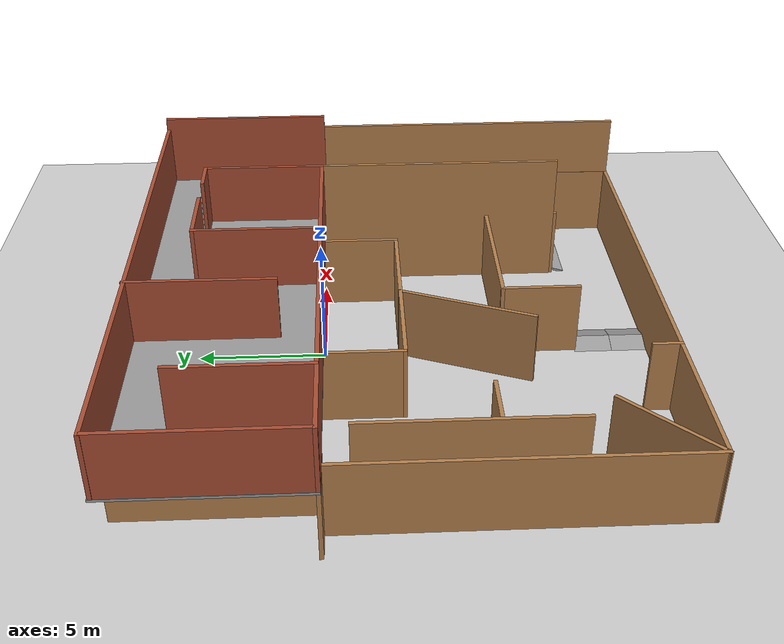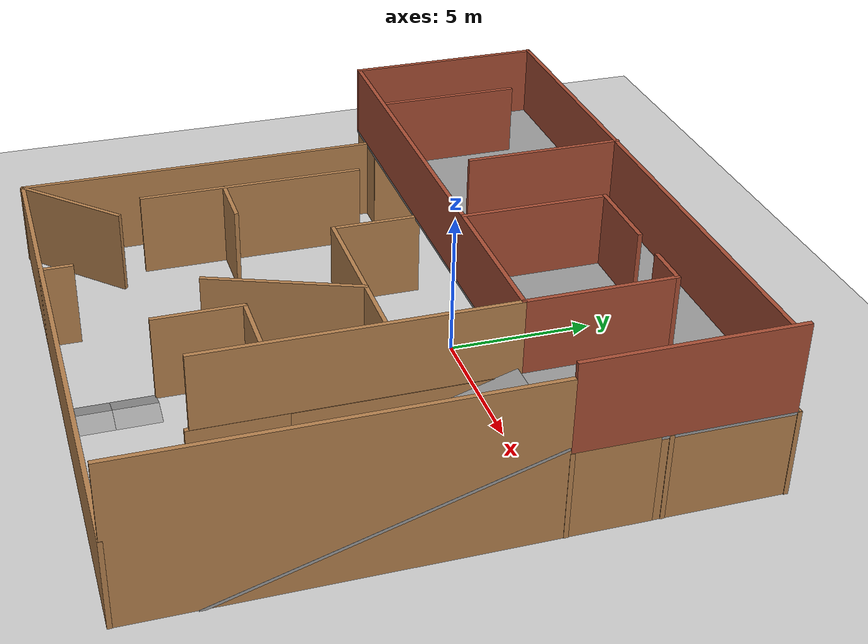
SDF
<sdf version="1.7">
 <world name="default">
  <light name="sun" type="directional">
   <pose>0 0 10 0 -0 0</pose>
   <diffuse>0.8 0.8 0.8 1</diffuse>
   <specular>0.2 0.2 0.2 1</specular>
   <attenuation>
    <range>1000</range>
    <constant>0.9</constant>
    <linear>0.01</linear>
    <quadratic>0.001</quadratic>
   </attenuation>
   <direction>-0.5 0.1 -0.9</direction>
   <spot><inner_angle>0</inner_angle><outer_angle>0</outer_angle><falloff>0</falloff></spot>
  </light>
  <model name="ground_plane">
   <static>1</static>
   <link name="link">
    <collision name="collision">
     <geometry><plane><normal>0 0 1</normal><size>100 100</size></plane></geometry>
     <surface>
      <contact><collide_bitmask>65535</collide_bitmask></contact>
      <friction><ode><mu>100</mu><mu2>50</mu2></ode></friction>
     </surface>
    </collision>
    <visual name="visual">
     <cast_shadows>0</cast_shadows>
     <geometry><plane><normal>0 0 1</normal><size>100 100</size></plane></geometry>
     <material>
      <script><uri>file://media/materials/scripts/gazebo.material</uri><name>Gazebo/Grey</name></script>
     </material>
    </visual>
   </link>
  </model>
  <gravity>0 0 -9.8</gravity>
  <magnetic_field>6e-06 2.3e-05 -4.2e-05</magnetic_field>
  <atmosphere type="adiabatic"/>
  <physics name="default_physics" default="0" type="ode">
   <max_step_size>0.001</max_step_size>
   <real_time_factor>1</real_time_factor>
   <real_time_update_rate>1000</real_time_update_rate>
  </physics>
  <scene><ambient>0.4 0.4 0.4 1</ambient><background>0.7 0.7 0.7 1</background><shadows>1</shadows></scene>
  <spherical_coordinates>
   <surface_model>EARTH_WGS84</surface_model>
   <latitude_deg>0</latitude_deg>
   <longitude_deg>0</longitude_deg>
   <elevation>0</elevation>
   <heading_deg>0</heading_deg>
  </spherical_coordinates>
  <audio><device>default</device></audio>
  <model name="exploration_worlds1">
   <link name="Wall_1">
    <pose>-9.98447 -3.49997 0 0 -0 1.5708</pose>
    <visual name="Wall_1_Visual">
     <pose>0 0 1.5 0 -0 0</pose>
     <geometry><box><size>13.15 0.15 3</size></box></geometry>
     <material>
      <script><uri>file://media/materials/scripts/gazebo.material</uri><name>Gazebo/Wood</name></script>
      <ambient>1 1 1 1</ambient>
      <shader type="pixel"/>
     </material>
     <meta><layer>0</layer></meta>
    </visual>
    <collision name="Wall_1_Collision">
     <pose>0 0 1.5 0 -0 0</pose>
     <geometry><box><size>13.15 0.15 3</size></box></geometry>
     <surface>
      <friction>
       <ode><mu>1</mu><mu2>1</mu2><fdir1>0 0 0</fdir1><slip1>0</slip1><slip2>0</slip2></ode>
       <torsional>
        <coefficient>1</coefficient>
        <patch_radius>0</patch_radius>
        <surface_radius>0</surface_radius>
        <use_patch_radius>1</use_patch_radius>
        <ode><slip>0</slip></ode>
       </torsional>
      </friction>
      <bounce><restitution_coefficient>0</restitution_coefficient><threshold>1e+06</threshold></bounce>
      <contact>
       <collide_without_contact>0</collide_without_contact>
       <collide_without_contact_bitmask>1</collide_without_contact_bitmask>
       <collide_bitmask>1</collide_bitmask>
       <ode>
        <soft_cfm>0</soft_cfm>
        <soft_erp>0.2</soft_erp>
        <kp>1e+13</kp>
        <kd>1</kd>
        <max_vel>0.01</max_vel>
        <min_depth>0</min_depth>
       </ode>
       <bullet>
        <split_impulse>1</split_impulse>
        <split_impulse_penetration_threshold>-0.01</split_impulse_penetration_threshold>
        <soft_cfm>0</soft_cfm>
        <soft_erp>0.2</soft_erp>
        <kp>1e+13</kp>
        <kd>1</kd>
       </bullet>
      </contact>
     </surface>
    </collision>
   </link>
   <link name="Wall_10">
    <pose>6.00253 8.01353 0 0 -0 1.5708</pose>
    <visual name="Wall_10_Visual">
     <pose>0 0 1.5 0 -0 0</pose>
     <geometry><box><size>4.123 0.15 3</size></box></geometry>
     <material>
      <script><uri>file://media/materials/scripts/gazebo.material</uri><name>Gazebo/Wood</name></script>
      <ambient>1 1 1 1</ambient>
      <shader type="pixel"/>
     </material>
     <meta><layer>0</layer></meta>
    </visual>
    <collision name="Wall_10_Collision">
     <pose>0 0 1.5 0 -0 0</pose>
     <geometry><box><size>4.123 0.15 3</size></box></geometry>
     <surface>
      <friction>
       <ode><mu>1</mu><mu2>1</mu2><fdir1>0 0 0</fdir1><slip1>0</slip1><slip2>0</slip2></ode>
       <torsional>
        <coefficient>1</coefficient>
        <patch_radius>0</patch_radius>
        <surface_radius>0</surface_radius>
        <use_patch_radius>1</use_patch_radius>
        <ode><slip>0</slip></ode>
       </torsional>
      </friction>
      <bounce><restitution_coefficient>0</restitution_coefficient><threshold>1e+06</threshold></bounce>
      <contact>
       <collide_without_contact>0</collide_without_contact>
       <collide_without_contact_bitmask>1</collide_without_contact_bitmask>
       <collide_bitmask>1</collide_bitmask>
       <ode>
        <soft_cfm>0</soft_cfm>
        <soft_erp>0.2</soft_erp>
        <kp>1e+13</kp>
        <kd>1</kd>
        <max_vel>0.01</max_vel>
        <min_depth>0</min_depth>
       </ode>
       <bullet>
        <split_impulse>1</split_impulse>
        <split_impulse_penetration_threshold>-0.01</split_impulse_penetration_threshold>
        <soft_cfm>0</soft_cfm>
        <soft_erp>0.2</soft_erp>
        <kp>1e+13</kp>
        <kd>1</kd>
       </bullet>
      </contact>
     </surface>
    </collision>
   </link>
   <link name="Wall_12">
    <pose>8.51553 6.00003 0 0 -0 0</pose>
    <visual name="Wall_12_Visual">
     <pose>0 0 1.5 0 -0 0</pose>
     <geometry><box><size>3.15 0.15 3</size></box></geometry>
     <material>
      <script><uri>file://media/materials/scripts/gazebo.material</uri><name>Gazebo/Wood</name></script>
      <ambient>1 1 1 1</ambient>
      <shader type="pixel"/>
     </material>
     <meta><layer>0</layer></meta>
    </visual>
    <collision name="Wall_12_Collision">
     <pose>0 0 1.5 0 -0 0</pose>
     <geometry><box><size>3.15 0.15 3</size></box></geometry>
     <surface>
      <friction>
       <ode><mu>1</mu><mu2>1</mu2><fdir1>0 0 0</fdir1><slip1>0</slip1><slip2>0</slip2></ode>
       <torsional>
        <coefficient>1</coefficient>
        <patch_radius>0</patch_radius>
        <surface_radius>0</surface_radius>
        <use_patch_radius>1</use_patch_radius>
        <ode><slip>0</slip></ode>
       </torsional>
      </friction>
      <bounce><restitution_coefficient>0</restitution_coefficient><threshold>1e+06</threshold></bounce>
      <contact>
       <collide_without_contact>0</collide_without_contact>
       <collide_without_contact_bitmask>1</collide_without_contact_bitmask>
       <collide_bitmask>1</collide_bitmask>
       <ode>
        <soft_cfm>0</soft_cfm>
        <soft_erp>0.2</soft_erp>
        <kp>1e+13</kp>
        <kd>1</kd>
        <max_vel>0.01</max_vel>
        <min_depth>0</min_depth>
       </ode>
       <bullet>
        <split_impulse>1</split_impulse>
        <split_impulse_penetration_threshold>-0.01</split_impulse_penetration_threshold>
        <soft_cfm>0</soft_cfm>
        <soft_erp>0.2</soft_erp>
        <kp>1e+13</kp>
        <kd>1</kd>
       </bullet>
      </contact>
     </surface>
    </collision>
   </link>
   <link name="Wall_14">
    <pose>2.51553 6.00003 0 0 -0 0</pose>
    <visual name="Wall_14_Visual">
     <pose>0 0 1.5 0 -0 0</pose>
     <geometry><box><size>5.15 0.15 3</size></box></geometry>
     <material>
      <script><uri>file://media/materials/scripts/gazebo.material</uri><name>Gazebo/Wood</name></script>
      <ambient>1 1 1 1</ambient>
      <shader type="pixel"/>
     </material>
     <meta><layer>0</layer></meta>
    </visual>
    <collision name="Wall_14_Collision">
     <pose>0 0 1.5 0 -0 0</pose>
     <geometry><box><size>5.15 0.15 3</size></box></geometry>
     <surface>
      <friction>
       <ode><mu>1</mu><mu2>1</mu2><fdir1>0 0 0</fdir1><slip1>0</slip1><slip2>0</slip2></ode>
       <torsional>
        <coefficient>1</coefficient>
        <patch_radius>0</patch_radius>
        <surface_radius>0</surface_radius>
        <use_patch_radius>1</use_patch_radius>
        <ode><slip>0</slip></ode>
       </torsional>
      </friction>
      <bounce><restitution_coefficient>0</restitution_coefficient><threshold>1e+06</threshold></bounce>
      <contact>
       <collide_without_contact>0</collide_without_contact>
       <collide_without_contact_bitmask>1</collide_without_contact_bitmask>
       <collide_bitmask>1</collide_bitmask>
       <ode>
        <soft_cfm>0</soft_cfm>
        <soft_erp>0.2</soft_erp>
        <kp>1e+13</kp>
        <kd>1</kd>
        <max_vel>0.01</max_vel>
        <min_depth>0</min_depth>
       </ode>
       <bullet>
        <split_impulse>1</split_impulse>
        <split_impulse_penetration_threshold>-0.01</split_impulse_penetration_threshold>
        <soft_cfm>0</soft_cfm>
        <soft_erp>0.2</soft_erp>
        <kp>1e+13</kp>
        <kd>1</kd>
       </bullet>
      </contact>
     </surface>
    </collision>
   </link>
   <link name="Wall_16">
    <pose>0.015533 8.00003 0 0 -0 1.5708</pose>
    <visual name="Wall_16_Visual">
     <pose>0 0 1.5 0 -0 0</pose>
     <geometry><box><size>4.15 0.15 3</size></box></geometry>
     <material>
      <script><uri>file://media/materials/scripts/gazebo.material</uri><name>Gazebo/Wood</name></script>
      <ambient>1 1 1 1</ambient>
      <shader type="pixel"/>
     </material>
     <meta><layer>0</layer></meta>
    </visual>
    <collision name="Wall_16_Collision">
     <pose>0 0 1.5 0 -0 0</pose>
     <geometry><box><size>4.15 0.15 3</size></box></geometry>
     <surface>
      <friction>
       <ode><mu>1</mu><mu2>1</mu2><fdir1>0 0 0</fdir1><slip1>0</slip1><slip2>0</slip2></ode>
       <torsional>
        <coefficient>1</coefficient>
        <patch_radius>0</patch_radius>
        <surface_radius>0</surface_radius>
        <use_patch_radius>1</use_patch_radius>
        <ode><slip>0</slip></ode>
       </torsional>
      </friction>
      <bounce><restitution_coefficient>0</restitution_coefficient><threshold>1e+06</threshold></bounce>
      <contact>
       <collide_without_contact>0</collide_without_contact>
       <collide_without_contact_bitmask>1</collide_without_contact_bitmask>
       <collide_bitmask>1</collide_bitmask>
       <ode>
        <soft_cfm>0</soft_cfm>
        <soft_erp>0.2</soft_erp>
        <kp>1e+13</kp>
        <kd>1</kd>
        <max_vel>0.01</max_vel>
        <min_depth>0</min_depth>
       </ode>
       <bullet>
        <split_impulse>1</split_impulse>
        <split_impulse_penetration_threshold>-0.01</split_impulse_penetration_threshold>
        <soft_cfm>0</soft_cfm>
        <soft_erp>0.2</soft_erp>
        <kp>1e+13</kp>
        <kd>1</kd>
       </bullet>
      </contact>
     </surface>
    </collision>
   </link>
   <link name="Wall_18">
    <pose>-4.98447 6.00003 0 0 -0 3.14159</pose>
    <visual name="Wall_18_Visual">
     <pose>0 0 1.5 0 -0 0</pose>
     <geometry><box><size>2.15 0.15 3</size></box></geometry>
     <material>
      <script><uri>file://media/materials/scripts/gazebo.material</uri><name>Gazebo/Wood</name></script>
      <ambient>1 1 1 1</ambient>
      <shader type="pixel"/>
     </material>
     <meta><layer>0</layer></meta>
    </visual>
    <collision name="Wall_18_Collision">
     <pose>0 0 1.5 0 -0 0</pose>
     <geometry><box><size>2.15 0.15 3</size></box></geometry>
     <surface>
      <friction>
       <ode><mu>1</mu><mu2>1</mu2><fdir1>0 0 0</fdir1><slip1>0</slip1><slip2>0</slip2></ode>
       <torsional>
        <coefficient>1</coefficient>
        <patch_radius>0</patch_radius>
        <surface_radius>0</surface_radius>
        <use_patch_radius>1</use_patch_radius>
        <ode><slip>0</slip></ode>
       </torsional>
      </friction>
      <bounce><restitution_coefficient>0</restitution_coefficient><threshold>1e+06</threshold></bounce>
      <contact>
       <collide_without_contact>0</collide_without_contact>
       <collide_without_contact_bitmask>1</collide_without_contact_bitmask>
       <collide_bitmask>1</collide_bitmask>
       <ode>
        <soft_cfm>0</soft_cfm>
        <soft_erp>0.2</soft_erp>
        <kp>1e+13</kp>
        <kd>1</kd>
        <max_vel>0.01</max_vel>
        <min_depth>0</min_depth>
       </ode>
       <bullet>
        <split_impulse>1</split_impulse>
        <split_impulse_penetration_threshold>-0.01</split_impulse_penetration_threshold>
        <soft_cfm>0</soft_cfm>
        <soft_erp>0.2</soft_erp>
        <kp>1e+13</kp>
        <kd>1</kd>
       </bullet>
      </contact>
     </surface>
    </collision>
   </link>
   <link name="Wall_20">
    <pose>-5.98447 8.03103 0 0 -0 1.5708</pose>
    <visual name="Wall_20_Visual">
     <pose>0 0 1.5 0 -0 0</pose>
     <geometry><box><size>4.15 0.15 3</size></box></geometry>
     <material>
      <script><uri>file://media/materials/scripts/gazebo.material</uri><name>Gazebo/Wood</name></script>
      <ambient>1 1 1 1</ambient>
      <shader type="pixel"/>
     </material>
     <meta><layer>0</layer></meta>
    </visual>
    <collision name="Wall_20_Collision">
     <pose>0 0 1.5 0 -0 0</pose>
     <geometry><box><size>4.15 0.15 3</size></box></geometry>
     <surface>
      <friction>
       <ode><mu>1</mu><mu2>1</mu2><fdir1>0 0 0</fdir1><slip1>0</slip1><slip2>0</slip2></ode>
       <torsional>
        <coefficient>1</coefficient>
        <patch_radius>0</patch_radius>
        <surface_radius>0</surface_radius>
        <use_patch_radius>1</use_patch_radius>
        <ode><slip>0</slip></ode>
       </torsional>
      </friction>
      <bounce><restitution_coefficient>0</restitution_coefficient><threshold>1e+06</threshold></bounce>
      <contact>
       <collide_without_contact>0</collide_without_contact>
       <collide_without_contact_bitmask>1</collide_without_contact_bitmask>
       <collide_bitmask>1</collide_bitmask>
       <ode>
        <soft_cfm>0</soft_cfm>
        <soft_erp>0.2</soft_erp>
        <kp>1e+13</kp>
        <kd>1</kd>
        <max_vel>0.01</max_vel>
        <min_depth>0</min_depth>
       </ode>
       <bullet>
        <split_impulse>1</split_impulse>
        <split_impulse_penetration_threshold>-0.01</split_impulse_penetration_threshold>
        <soft_cfm>0</soft_cfm>
        <soft_erp>0.2</soft_erp>
        <kp>1e+13</kp>
        <kd>1</kd>
       </bullet>
      </contact>
     </surface>
    </collision>
   </link>
   <link name="Wall_22">
    <pose>-9.01547 6.53103 0 0 0 -1.5708</pose>
    <visual name="Wall_22_Visual">
     <pose>0 0 1.5 0 -0 0</pose>
     <geometry><box><size>7.15 0.15 3</size></box></geometry>
     <material>
      <script><uri>file://media/materials/scripts/gazebo.material</uri><name>Gazebo/Wood</name></script>
      <ambient>1 1 1 1</ambient>
      <shader type="pixel"/>
     </material>
     <meta><layer>0</layer></meta>
    </visual>
    <collision name="Wall_22_Collision">
     <pose>0 0 1.5 0 -0 0</pose>
     <geometry><box><size>7.15 0.15 3</size></box></geometry>
     <surface>
      <friction>
       <ode><mu>1</mu><mu2>1</mu2><fdir1>0 0 0</fdir1><slip1>0</slip1><slip2>0</slip2></ode>
       <torsional>
        <coefficient>1</coefficient>
        <patch_radius>0</patch_radius>
        <surface_radius>0</surface_radius>
        <use_patch_radius>1</use_patch_radius>
        <ode><slip>0</slip></ode>
       </torsional>
      </friction>
      <bounce><restitution_coefficient>0</restitution_coefficient><threshold>1e+06</threshold></bounce>
      <contact>
       <collide_without_contact>0</collide_without_contact>
       <collide_without_contact_bitmask>1</collide_without_contact_bitmask>
       <collide_bitmask>1</collide_bitmask>
       <ode>
        <soft_cfm>0</soft_cfm>
        <soft_erp>0.2</soft_erp>
        <kp>1e+13</kp>
        <kd>1</kd>
        <max_vel>0.01</max_vel>
        <min_depth>0</min_depth>
       </ode>
       <bullet>
        <split_impulse>1</split_impulse>
        <split_impulse_penetration_threshold>-0.01</split_impulse_penetration_threshold>
        <soft_cfm>0</soft_cfm>
        <soft_erp>0.2</soft_erp>
        <kp>1e+13</kp>
        <kd>1</kd>
       </bullet>
      </contact>
     </surface>
    </collision>
   </link>
   <link name="Wall_24">
    <pose>0.515533 10 0 0 -0 0</pose>
    <visual name="Wall_24_Visual">
     <pose>0 0 1.5 0 -0 0</pose>
     <geometry><box><size>19.15 0.15 3</size></box></geometry>
     <material>
      <script><uri>file://media/materials/scripts/gazebo.material</uri><name>Gazebo/Wood</name></script>
      <ambient>1 1 1 1</ambient>
      <shader type="pixel"/>
     </material>
     <meta><layer>0</layer></meta>
    </visual>
    <collision name="Wall_24_Collision">
     <pose>0 0 1.5 0 -0 0</pose>
     <geometry><box><size>19.15 0.15 3</size></box></geometry>
     <surface>
      <friction>
       <ode><mu>1</mu><mu2>1</mu2><fdir1>0 0 0</fdir1><slip1>0</slip1><slip2>0</slip2></ode>
       <torsional>
        <coefficient>1</coefficient>
        <patch_radius>0</patch_radius>
        <surface_radius>0</surface_radius>
        <use_patch_radius>1</use_patch_radius>
        <ode><slip>0</slip></ode>
       </torsional>
      </friction>
      <bounce><restitution_coefficient>0</restitution_coefficient><threshold>1e+06</threshold></bounce>
      <contact>
       <collide_without_contact>0</collide_without_contact>
       <collide_without_contact_bitmask>1</collide_without_contact_bitmask>
       <collide_bitmask>1</collide_bitmask>
       <ode>
        <soft_cfm>0</soft_cfm>
        <soft_erp>0.2</soft_erp>
        <kp>1e+13</kp>
        <kd>1</kd>
        <max_vel>0.01</max_vel>
        <min_depth>0</min_depth>
       </ode>
       <bullet>
        <split_impulse>1</split_impulse>
        <split_impulse_penetration_threshold>-0.01</split_impulse_penetration_threshold>
        <soft_cfm>0</soft_cfm>
        <soft_erp>0.2</soft_erp>
        <kp>1e+13</kp>
        <kd>1</kd>
       </bullet>
      </contact>
     </surface>
    </collision>
   </link>
   <link name="Wall_26">
    <pose>0.015533 3.3e-05 0 0 -0 0</pose>
    <visual name="Wall_26_Visual">
     <pose>0 0 1.5 0 -0 0</pose>
     <geometry><box><size>8.15 0.15 3</size></box></geometry>
     <material>
      <script><uri>file://media/materials/scripts/gazebo.material</uri><name>Gazebo/Wood</name></script>
      <ambient>1 1 1 1</ambient>
      <shader type="pixel"/>
     </material>
     <meta><layer>0</layer></meta>
    </visual>
    <collision name="Wall_26_Collision">
     <pose>0 0 1.5 0 -0 0</pose>
     <geometry><box><size>8.15 0.15 3</size></box></geometry>
     <surface>
      <friction>
       <ode><mu>1</mu><mu2>1</mu2><fdir1>0 0 0</fdir1><slip1>0</slip1><slip2>0</slip2></ode>
       <torsional>
        <coefficient>1</coefficient>
        <patch_radius>0</patch_radius>
        <surface_radius>0</surface_radius>
        <use_patch_radius>1</use_patch_radius>
        <ode><slip>0</slip></ode>
       </torsional>
      </friction>
      <bounce><restitution_coefficient>0</restitution_coefficient><threshold>1e+06</threshold></bounce>
      <contact>
       <collide_without_contact>0</collide_without_contact>
       <collide_without_contact_bitmask>1</collide_without_contact_bitmask>
       <collide_bitmask>1</collide_bitmask>
       <ode>
        <soft_cfm>0</soft_cfm>
        <soft_erp>0.2</soft_erp>
        <kp>1e+13</kp>
        <kd>1</kd>
        <max_vel>0.01</max_vel>
        <min_depth>0</min_depth>
       </ode>
       <bullet>
        <split_impulse>1</split_impulse>
        <split_impulse_penetration_threshold>-0.01</split_impulse_penetration_threshold>
        <soft_cfm>0</soft_cfm>
        <soft_erp>0.2</soft_erp>
        <kp>1e+13</kp>
        <kd>1</kd>
       </bullet>
      </contact>
     </surface>
    </collision>
   </link>
   <link name="Wall_28">
    <pose>-3.98447 1.53103 0 0 -0 1.5708</pose>
    <visual name="Wall_28_Visual">
     <pose>0 0 1.5 0 -0 0</pose>
     <geometry><box><size>3.15 0.15 3</size></box></geometry>
     <material>
      <script><uri>file://media/materials/scripts/gazebo.material</uri><name>Gazebo/Wood</name></script>
      <ambient>1 1 1 1</ambient>
      <shader type="pixel"/>
     </material>
     <meta><layer>0</layer></meta>
    </visual>
    <collision name="Wall_28_Collision">
     <pose>0 0 1.5 0 -0 0</pose>
     <geometry><box><size>3.15 0.15 3</size></box></geometry>
     <surface>
      <friction>
       <ode><mu>1</mu><mu2>1</mu2><fdir1>0 0 0</fdir1><slip1>0</slip1><slip2>0</slip2></ode>
       <torsional>
        <coefficient>1</coefficient>
        <patch_radius>0</patch_radius>
        <surface_radius>0</surface_radius>
        <use_patch_radius>1</use_patch_radius>
        <ode><slip>0</slip></ode>
       </torsional>
      </friction>
      <bounce><restitution_coefficient>0</restitution_coefficient><threshold>1e+06</threshold></bounce>
      <contact>
       <collide_without_contact>0</collide_without_contact>
       <collide_without_contact_bitmask>1</collide_without_contact_bitmask>
       <collide_bitmask>1</collide_bitmask>
       <ode>
        <soft_cfm>0</soft_cfm>
        <soft_erp>0.2</soft_erp>
        <kp>1e+13</kp>
        <kd>1</kd>
        <max_vel>0.01</max_vel>
        <min_depth>0</min_depth>
       </ode>
       <bullet>
        <split_impulse>1</split_impulse>
        <split_impulse_penetration_threshold>-0.01</split_impulse_penetration_threshold>
        <soft_cfm>0</soft_cfm>
        <soft_erp>0.2</soft_erp>
        <kp>1e+13</kp>
        <kd>1</kd>
       </bullet>
      </contact>
     </surface>
    </collision>
   </link>
   <link name="Wall_30">
    <pose>-7.98447 6.00003 0 0 -0 3.14159</pose>
    <visual name="Wall_30_Visual">
     <pose>0 0 1.5 0 -0 0</pose>
     <geometry><box><size>2.15 0.15 3</size></box></geometry>
     <material>
      <script><uri>file://media/materials/scripts/gazebo.material</uri><name>Gazebo/Wood</name></script>
      <ambient>1 1 1 1</ambient>
      <shader type="pixel"/>
     </material>
     <meta><layer>0</layer></meta>
    </visual>
    <collision name="Wall_30_Collision">
     <pose>0 0 1.5 0 -0 0</pose>
     <geometry><box><size>2.15 0.15 3</size></box></geometry>
     <surface>
      <friction>
       <ode><mu>1</mu><mu2>1</mu2><fdir1>0 0 0</fdir1><slip1>0</slip1><slip2>0</slip2></ode>
       <torsional>
        <coefficient>1</coefficient>
        <patch_radius>0</patch_radius>
        <surface_radius>0</surface_radius>
        <use_patch_radius>1</use_patch_radius>
        <ode><slip>0</slip></ode>
       </torsional>
      </friction>
      <bounce><restitution_coefficient>0</restitution_coefficient><threshold>1e+06</threshold></bounce>
      <contact>
       <collide_without_contact>0</collide_without_contact>
       <collide_without_contact_bitmask>1</collide_without_contact_bitmask>
       <collide_bitmask>1</collide_bitmask>
       <ode>
        <soft_cfm>0</soft_cfm>
        <soft_erp>0.2</soft_erp>
        <kp>1e+13</kp>
        <kd>1</kd>
        <max_vel>0.01</max_vel>
        <min_depth>0</min_depth>
       </ode>
       <bullet>
        <split_impulse>1</split_impulse>
        <split_impulse_penetration_threshold>-0.01</split_impulse_penetration_threshold>
        <soft_cfm>0</soft_cfm>
        <soft_erp>0.2</soft_erp>
        <kp>1e+13</kp>
        <kd>1</kd>
       </bullet>
      </contact>
     </surface>
    </collision>
   </link>
   <link name="Wall_30_clone">
    <pose>-10.0342 3.0218 0 0 -0 3.14159</pose>
    <visual name="Wall_30_Visual">
     <pose>0 0 1.5 0 -0 0</pose>
     <geometry><box><size>2.15 0.15 3</size></box></geometry>
     <material>
      <script><uri>file://media/materials/scripts/gazebo.material</uri><name>Gazebo/Wood</name></script>
      <ambient>1 1 1 1</ambient>
      <shader type="pixel"/>
     </material>
     <meta><layer>0</layer></meta>
    </visual>
    <collision name="Wall_30_Collision">
     <pose>0 0 1.5 0 -0 0</pose>
     <geometry><box><size>2.15 0.15 3</size></box></geometry>
     <surface>
      <friction>
       <ode><mu>1</mu><mu2>1</mu2><fdir1>0 0 0</fdir1><slip1>0</slip1><slip2>0</slip2></ode>
       <torsional>
        <coefficient>1</coefficient>
        <patch_radius>0</patch_radius>
        <surface_radius>0</surface_radius>
        <use_patch_radius>1</use_patch_radius>
        <ode><slip>0</slip></ode>
       </torsional>
      </friction>
      <bounce><restitution_coefficient>0</restitution_coefficient><threshold>1e+06</threshold></bounce>
      <contact>
       <collide_without_contact>0</collide_without_contact>
       <collide_without_contact_bitmask>1</collide_without_contact_bitmask>
       <collide_bitmask>1</collide_bitmask>
       <ode>
        <soft_cfm>0</soft_cfm>
        <soft_erp>0.2</soft_erp>
        <kp>1e+13</kp>
        <kd>1</kd>
        <max_vel>0.01</max_vel>
        <min_depth>0</min_depth>
       </ode>
       <bullet>
        <split_impulse>1</split_impulse>
        <split_impulse_penetration_threshold>-0.01</split_impulse_penetration_threshold>
        <soft_cfm>0</soft_cfm>
        <soft_erp>0.2</soft_erp>
        <kp>1e+13</kp>
        <kd>1</kd>
       </bullet>
      </contact>
     </surface>
    </collision>
   </link>
   <link name="Wall_32">
    <pose>4.01553 1.50003 0 0 -0 1.5708</pose>
    <visual name="Wall_32_Visual">
     <pose>0 0 1.5 0 -0 0</pose>
     <geometry><box><size>3.15 0.15 3</size></box></geometry>
     <material>
      <script><uri>file://media/materials/scripts/gazebo.material</uri><name>Gazebo/Wood</name></script>
      <ambient>1 1 1 1</ambient>
      <shader type="pixel"/>
     </material>
     <meta><layer>0</layer></meta>
    </visual>
    <collision name="Wall_32_Collision">
     <pose>0 0 1.5 0 -0 0</pose>
     <geometry><box><size>3.15 0.15 3</size></box></geometry>
     <surface>
      <friction>
       <ode><mu>1</mu><mu2>1</mu2><fdir1>0 0 0</fdir1><slip1>0</slip1><slip2>0</slip2></ode>
       <torsional>
        <coefficient>1</coefficient>
        <patch_radius>0</patch_radius>
        <surface_radius>0</surface_radius>
        <use_patch_radius>1</use_patch_radius>
        <ode><slip>0</slip></ode>
       </torsional>
      </friction>
      <bounce><restitution_coefficient>0</restitution_coefficient><threshold>1e+06</threshold></bounce>
      <contact>
       <collide_without_contact>0</collide_without_contact>
       <collide_without_contact_bitmask>1</collide_without_contact_bitmask>
       <collide_bitmask>1</collide_bitmask>
       <ode>
        <soft_cfm>0</soft_cfm>
        <soft_erp>0.2</soft_erp>
        <kp>1e+13</kp>
        <kd>1</kd>
        <max_vel>0.01</max_vel>
        <min_depth>0</min_depth>
       </ode>
       <bullet>
        <split_impulse>1</split_impulse>
        <split_impulse_penetration_threshold>-0.01</split_impulse_penetration_threshold>
        <soft_cfm>0</soft_cfm>
        <soft_erp>0.2</soft_erp>
        <kp>1e+13</kp>
        <kd>1</kd>
       </bullet>
      </contact>
     </surface>
    </collision>
   </link>
   <link name="Wall_34">
    <pose>8.51553 3.00003 0 0 -0 0</pose>
    <visual name="Wall_34_Visual">
     <pose>0 0 1.5 0 -0 0</pose>
     <geometry><box><size>3.15 0.15 3</size></box></geometry>
     <material>
      <script><uri>file://media/materials/scripts/gazebo.material</uri><name>Gazebo/Wood</name></script>
      <ambient>1 1 1 1</ambient>
      <shader type="pixel"/>
     </material>
     <meta><layer>0</layer></meta>
    </visual>
    <collision name="Wall_34_Collision">
     <pose>0 0 1.5 0 -0 0</pose>
     <geometry><box><size>3.15 0.15 3</size></box></geometry>
     <surface>
      <friction>
       <ode><mu>1</mu><mu2>1</mu2><fdir1>0 0 0</fdir1><slip1>0</slip1><slip2>0</slip2></ode>
       <torsional>
        <coefficient>1</coefficient>
        <patch_radius>0</patch_radius>
        <surface_radius>0</surface_radius>
        <use_patch_radius>1</use_patch_radius>
        <ode><slip>0</slip></ode>
       </torsional>
      </friction>
      <bounce><restitution_coefficient>0</restitution_coefficient><threshold>1e+06</threshold></bounce>
      <contact>
       <collide_without_contact>0</collide_without_contact>
       <collide_without_contact_bitmask>1</collide_without_contact_bitmask>
       <collide_bitmask>1</collide_bitmask>
       <ode>
        <soft_cfm>0</soft_cfm>
        <soft_erp>0.2</soft_erp>
        <kp>1e+13</kp>
        <kd>1</kd>
        <max_vel>0.01</max_vel>
        <min_depth>0</min_depth>
       </ode>
       <bullet>
        <split_impulse>1</split_impulse>
        <split_impulse_penetration_threshold>-0.01</split_impulse_penetration_threshold>
        <soft_cfm>0</soft_cfm>
        <soft_erp>0.2</soft_erp>
        <kp>1e+13</kp>
        <kd>1</kd>
       </bullet>
      </contact>
     </surface>
    </collision>
   </link>
   <link name="Wall_36">
    <pose>0.015533 -5.49997 0 0 0 -1.5708</pose>
    <visual name="Wall_36_Visual">
     <pose>0 0 1.5 0 -0 0</pose>
     <geometry><box><size>3.15 0.15 3</size></box></geometry>
     <material>
      <script><uri>file://media/materials/scripts/gazebo.material</uri><name>Gazebo/Wood</name></script>
      <ambient>1 1 1 1</ambient>
      <shader type="pixel"/>
     </material>
     <meta><layer>0</layer></meta>
    </visual>
    <collision name="Wall_36_Collision">
     <pose>0 0 1.5 0 -0 0</pose>
     <geometry><box><size>3.15 0.15 3</size></box></geometry>
     <surface>
      <friction>
       <ode><mu>1</mu><mu2>1</mu2><fdir1>0 0 0</fdir1><slip1>0</slip1><slip2>0</slip2></ode>
       <torsional>
        <coefficient>1</coefficient>
        <patch_radius>0</patch_radius>
        <surface_radius>0</surface_radius>
        <use_patch_radius>1</use_patch_radius>
        <ode><slip>0</slip></ode>
       </torsional>
      </friction>
      <bounce><restitution_coefficient>0</restitution_coefficient><threshold>1e+06</threshold></bounce>
      <contact>
       <collide_without_contact>0</collide_without_contact>
       <collide_without_contact_bitmask>1</collide_without_contact_bitmask>
       <collide_bitmask>1</collide_bitmask>
       <ode>
        <soft_cfm>0</soft_cfm>
        <soft_erp>0.2</soft_erp>
        <kp>1e+13</kp>
        <kd>1</kd>
        <max_vel>0.01</max_vel>
        <min_depth>0</min_depth>
       </ode>
       <bullet>
        <split_impulse>1</split_impulse>
        <split_impulse_penetration_threshold>-0.01</split_impulse_penetration_threshold>
        <soft_cfm>0</soft_cfm>
        <soft_erp>0.2</soft_erp>
        <kp>1e+13</kp>
        <kd>1</kd>
       </bullet>
      </contact>
     </surface>
    </collision>
   </link>
   <link name="Wall_38">
    <pose>3.01553 -3.99997 0 0 -0 0</pose>
    <visual name="Wall_38_Visual">
     <pose>0 0 1.5 0 -0 0</pose>
     <geometry><box><size>6.15 0.15 3</size></box></geometry>
     <material>
      <script><uri>file://media/materials/scripts/gazebo.material</uri><name>Gazebo/Wood</name></script>
      <ambient>1 1 1 1</ambient>
      <shader type="pixel"/>
     </material>
     <meta><layer>0</layer></meta>
    </visual>
    <collision name="Wall_38_Collision">
     <pose>0 0 1.5 0 -0 0</pose>
     <geometry><box><size>6.15 0.15 3</size></box></geometry>
     <surface>
      <friction>
       <ode><mu>1</mu><mu2>1</mu2><fdir1>0 0 0</fdir1><slip1>0</slip1><slip2>0</slip2></ode>
       <torsional>
        <coefficient>1</coefficient>
        <patch_radius>0</patch_radius>
        <surface_radius>0</surface_radius>
        <use_patch_radius>1</use_patch_radius>
        <ode><slip>0</slip></ode>
       </torsional>
      </friction>
      <bounce><restitution_coefficient>0</restitution_coefficient><threshold>1e+06</threshold></bounce>
      <contact>
       <collide_without_contact>0</collide_without_contact>
       <collide_without_contact_bitmask>1</collide_without_contact_bitmask>
       <collide_bitmask>1</collide_bitmask>
       <ode>
        <soft_cfm>0</soft_cfm>
        <soft_erp>0.2</soft_erp>
        <kp>1e+13</kp>
        <kd>1</kd>
        <max_vel>0.01</max_vel>
        <min_depth>0</min_depth>
       </ode>
       <bullet>
        <split_impulse>1</split_impulse>
        <split_impulse_penetration_threshold>-0.01</split_impulse_penetration_threshold>
        <soft_cfm>0</soft_cfm>
        <soft_erp>0.2</soft_erp>
        <kp>1e+13</kp>
        <kd>1</kd>
       </bullet>
      </contact>
     </surface>
    </collision>
   </link>
   <link name="Wall_40">
    <pose>6.01553 -5.49997 0 0 0 -1.5708</pose>
    <visual name="Wall_40_Visual">
     <pose>0 0 1.5 0 -0 0</pose>
     <geometry><box><size>3.15 0.15 3</size></box></geometry>
     <material>
      <script><uri>file://media/materials/scripts/gazebo.material</uri><name>Gazebo/Wood</name></script>
      <ambient>1 1 1 1</ambient>
      <shader type="pixel"/>
     </material>
     <meta><layer>0</layer></meta>
    </visual>
    <collision name="Wall_40_Collision">
     <pose>0 0 1.5 0 -0 0</pose>
     <geometry><box><size>3.15 0.15 3</size></box></geometry>
     <surface>
      <friction>
       <ode><mu>1</mu><mu2>1</mu2><fdir1>0 0 0</fdir1><slip1>0</slip1><slip2>0</slip2></ode>
       <torsional>
        <coefficient>1</coefficient>
        <patch_radius>0</patch_radius>
        <surface_radius>0</surface_radius>
        <use_patch_radius>1</use_patch_radius>
        <ode><slip>0</slip></ode>
       </torsional>
      </friction>
      <bounce><restitution_coefficient>0</restitution_coefficient><threshold>1e+06</threshold></bounce>
      <contact>
       <collide_without_contact>0</collide_without_contact>
       <collide_without_contact_bitmask>1</collide_without_contact_bitmask>
       <collide_bitmask>1</collide_bitmask>
       <ode>
        <soft_cfm>0</soft_cfm>
        <soft_erp>0.2</soft_erp>
        <kp>1e+13</kp>
        <kd>1</kd>
        <max_vel>0.01</max_vel>
        <min_depth>0</min_depth>
       </ode>
       <bullet>
        <split_impulse>1</split_impulse>
        <split_impulse_penetration_threshold>-0.01</split_impulse_penetration_threshold>
        <soft_cfm>0</soft_cfm>
        <soft_erp>0.2</soft_erp>
        <kp>1e+13</kp>
        <kd>1</kd>
       </bullet>
      </contact>
     </surface>
    </collision>
   </link>
   <link name="Wall_42">
    <pose>-8.48447 -8.49997 0 0 -0 0.785398</pose>
    <visual name="Wall_42_Visual">
     <pose>0 0 1.5 0 -0 0</pose>
     <geometry><box><size>4.39264 0.15 3</size></box></geometry>
     <material>
      <script><uri>file://media/materials/scripts/gazebo.material</uri><name>Gazebo/Wood</name></script>
      <ambient>1 1 1 1</ambient>
      <shader type="pixel"/>
     </material>
     <meta><layer>0</layer></meta>
    </visual>
    <collision name="Wall_42_Collision">
     <pose>0 0 1.5 0 -0 0</pose>
     <geometry><box><size>4.39264 0.15 3</size></box></geometry>
     <surface>
      <friction>
       <ode><mu>1</mu><mu2>1</mu2><fdir1>0 0 0</fdir1><slip1>0</slip1><slip2>0</slip2></ode>
       <torsional>
        <coefficient>1</coefficient>
        <patch_radius>0</patch_radius>
        <surface_radius>0</surface_radius>
        <use_patch_radius>1</use_patch_radius>
        <ode><slip>0</slip></ode>
       </torsional>
      </friction>
      <bounce><restitution_coefficient>0</restitution_coefficient><threshold>1e+06</threshold></bounce>
      <contact>
       <collide_without_contact>0</collide_without_contact>
       <collide_without_contact_bitmask>1</collide_without_contact_bitmask>
       <collide_bitmask>1</collide_bitmask>
       <ode>
        <soft_cfm>0</soft_cfm>
        <soft_erp>0.2</soft_erp>
        <kp>1e+13</kp>
        <kd>1</kd>
        <max_vel>0.01</max_vel>
        <min_depth>0</min_depth>
       </ode>
       <bullet>
        <split_impulse>1</split_impulse>
        <split_impulse_penetration_threshold>-0.01</split_impulse_penetration_threshold>
        <soft_cfm>0</soft_cfm>
        <soft_erp>0.2</soft_erp>
        <kp>1e+13</kp>
        <kd>1</kd>
       </bullet>
      </contact>
     </surface>
    </collision>
   </link>
   <link name="Wall_44">
    <pose>-3.98447 -9.49997 0 0 -0 1.5708</pose>
    <visual name="Wall_44_Visual">
     <pose>0 0 1.5 0 -0 0</pose>
     <geometry><box><size>1.15 0.15 3</size></box></geometry>
     <material>
      <script><uri>file://media/materials/scripts/gazebo.material</uri><name>Gazebo/Wood</name></script>
      <ambient>1 1 1 1</ambient>
      <shader type="pixel"/>
     </material>
     <meta><layer>0</layer></meta>
    </visual>
    <collision name="Wall_44_Collision">
     <pose>0 0 1.5 0 -0 0</pose>
     <geometry><box><size>1.15 0.15 3</size></box></geometry>
     <surface>
      <friction>
       <ode><mu>1</mu><mu2>1</mu2><fdir1>0 0 0</fdir1><slip1>0</slip1><slip2>0</slip2></ode>
       <torsional>
        <coefficient>1</coefficient>
        <patch_radius>0</patch_radius>
        <surface_radius>0</surface_radius>
        <use_patch_radius>1</use_patch_radius>
        <ode><slip>0</slip></ode>
       </torsional>
      </friction>
      <bounce><restitution_coefficient>0</restitution_coefficient><threshold>1e+06</threshold></bounce>
      <contact>
       <collide_without_contact>0</collide_without_contact>
       <collide_without_contact_bitmask>1</collide_without_contact_bitmask>
       <collide_bitmask>1</collide_bitmask>
       <ode>
        <soft_cfm>0</soft_cfm>
        <soft_erp>0.2</soft_erp>
        <kp>1e+13</kp>
        <kd>1</kd>
        <max_vel>0.01</max_vel>
        <min_depth>0</min_depth>
       </ode>
       <bullet>
        <split_impulse>1</split_impulse>
        <split_impulse_penetration_threshold>-0.01</split_impulse_penetration_threshold>
        <soft_cfm>0</soft_cfm>
        <soft_erp>0.2</soft_erp>
        <kp>1e+13</kp>
        <kd>1</kd>
       </bullet>
      </contact>
     </surface>
    </collision>
   </link>
   <link name="Wall_46">
    <pose>-7.98447 -1.99997 0 0 0 -1.5708</pose>
    <visual name="Wall_46_Visual">
     <pose>0 0 1.5 0 -0 0</pose>
     <geometry><box><size>8.15 0.15 3</size></box></geometry>
     <material>
      <script><uri>file://media/materials/scripts/gazebo.material</uri><name>Gazebo/Wood</name></script>
      <ambient>1 1 1 1</ambient>
      <shader type="pixel"/>
     </material>
     <meta><layer>0</layer></meta>
    </visual>
    <collision name="Wall_46_Collision">
     <pose>0 0 1.5 0 -0 0</pose>
     <geometry><box><size>8.15 0.15 3</size></box></geometry>
     <surface>
      <friction>
       <ode><mu>1</mu><mu2>1</mu2><fdir1>0 0 0</fdir1><slip1>0</slip1><slip2>0</slip2></ode>
       <torsional>
        <coefficient>1</coefficient>
        <patch_radius>0</patch_radius>
        <surface_radius>0</surface_radius>
        <use_patch_radius>1</use_patch_radius>
        <ode><slip>0</slip></ode>
       </torsional>
      </friction>
      <bounce><restitution_coefficient>0</restitution_coefficient><threshold>1e+06</threshold></bounce>
      <contact>
       <collide_without_contact>0</collide_without_contact>
       <collide_without_contact_bitmask>1</collide_without_contact_bitmask>
       <collide_bitmask>1</collide_bitmask>
       <ode>
        <soft_cfm>0</soft_cfm>
        <soft_erp>0.2</soft_erp>
        <kp>1e+13</kp>
        <kd>1</kd>
        <max_vel>0.01</max_vel>
        <min_depth>0</min_depth>
       </ode>
       <bullet>
        <split_impulse>1</split_impulse>
        <split_impulse_penetration_threshold>-0.01</split_impulse_penetration_threshold>
        <soft_cfm>0</soft_cfm>
        <soft_erp>0.2</soft_erp>
        <kp>1e+13</kp>
        <kd>1</kd>
       </bullet>
      </contact>
     </surface>
    </collision>
   </link>
   <link name="Wall_48">
    <pose>-0.984467 -2.49997 0 0 0 -1.9513</pose>
    <visual name="Wall_48_Visual">
     <pose>0 0 1.5 0 -0 0</pose>
     <geometry><box><size>5.53517 0.15 3</size></box></geometry>
     <material>
      <script><uri>file://media/materials/scripts/gazebo.material</uri><name>Gazebo/Wood</name></script>
      <ambient>1 1 1 1</ambient>
      <shader type="pixel"/>
     </material>
     <meta><layer>0</layer></meta>
    </visual>
    <collision name="Wall_48_Collision">
     <pose>0 0 1.5 0 -0 0</pose>
     <geometry><box><size>5.53517 0.15 3</size></box></geometry>
     <surface>
      <friction>
       <ode><mu>1</mu><mu2>1</mu2><fdir1>0 0 0</fdir1><slip1>0</slip1><slip2>0</slip2></ode>
       <torsional>
        <coefficient>1</coefficient>
        <patch_radius>0</patch_radius>
        <surface_radius>0</surface_radius>
        <use_patch_radius>1</use_patch_radius>
        <ode><slip>0</slip></ode>
       </torsional>
      </friction>
      <bounce><restitution_coefficient>0</restitution_coefficient><threshold>1e+06</threshold></bounce>
      <contact>
       <collide_without_contact>0</collide_without_contact>
       <collide_without_contact_bitmask>1</collide_without_contact_bitmask>
       <collide_bitmask>1</collide_bitmask>
       <ode>
        <soft_cfm>0</soft_cfm>
        <soft_erp>0.2</soft_erp>
        <kp>1e+13</kp>
        <kd>1</kd>
        <max_vel>0.01</max_vel>
        <min_depth>0</min_depth>
       </ode>
       <bullet>
        <split_impulse>1</split_impulse>
        <split_impulse_penetration_threshold>-0.01</split_impulse_penetration_threshold>
        <soft_cfm>0</soft_cfm>
        <soft_erp>0.2</soft_erp>
        <kp>1e+13</kp>
        <kd>1</kd>
       </bullet>
      </contact>
     </surface>
    </collision>
   </link>
   <link name="Wall_50">
    <pose>-6.98447 -2.99997 0 0 -0 0</pose>
    <visual name="Wall_50_Visual">
     <pose>0 0 1.5 0 -0 0</pose>
     <geometry><box><size>2.15 0.15 3</size></box></geometry>
     <material>
      <script><uri>file://media/materials/scripts/gazebo.material</uri><name>Gazebo/Wood</name></script>
      <ambient>1 1 1 1</ambient>
      <shader type="pixel"/>
     </material>
     <meta><layer>0</layer></meta>
    </visual>
    <collision name="Wall_50_Collision">
     <pose>0 0 1.5 0 -0 0</pose>
     <geometry><box><size>2.15 0.15 3</size></box></geometry>
     <surface>
      <friction>
       <ode><mu>1</mu><mu2>1</mu2><fdir1>0 0 0</fdir1><slip1>0</slip1><slip2>0</slip2></ode>
       <torsional>
        <coefficient>1</coefficient>
        <patch_radius>0</patch_radius>
        <surface_radius>0</surface_radius>
        <use_patch_radius>1</use_patch_radius>
        <ode><slip>0</slip></ode>
       </torsional>
      </friction>
      <bounce><restitution_coefficient>0</restitution_coefficient><threshold>1e+06</threshold></bounce>
      <contact>
       <collide_without_contact>0</collide_without_contact>
       <collide_without_contact_bitmask>1</collide_without_contact_bitmask>
       <collide_bitmask>1</collide_bitmask>
       <ode>
        <soft_cfm>0</soft_cfm>
        <soft_erp>0.2</soft_erp>
        <kp>1e+13</kp>
        <kd>1</kd>
        <max_vel>0.01</max_vel>
        <min_depth>0</min_depth>
       </ode>
       <bullet>
        <split_impulse>1</split_impulse>
        <split_impulse_penetration_threshold>-0.01</split_impulse_penetration_threshold>
        <soft_cfm>0</soft_cfm>
        <soft_erp>0.2</soft_erp>
        <kp>1e+13</kp>
        <kd>1</kd>
       </bullet>
      </contact>
     </surface>
    </collision>
   </link>
   <link name="Wall_6">
    <pose>0.015533 -9.99997 0 0 -0 0</pose>
    <visual name="Wall_6_Visual">
     <pose>0 0 1.5 0 -0 0</pose>
     <geometry><box><size>20.15 0.15 3</size></box></geometry>
     <material>
      <script><uri>file://media/materials/scripts/gazebo.material</uri><name>Gazebo/Wood</name></script>
      <ambient>1 1 1 1</ambient>
      <shader type="pixel"/>
     </material>
     <meta><layer>0</layer></meta>
    </visual>
    <collision name="Wall_6_Collision">
     <pose>0 0 1.5 0 -0 0</pose>
     <geometry><box><size>20.15 0.15 3</size></box></geometry>
     <surface>
      <friction>
       <ode><mu>1</mu><mu2>1</mu2><fdir1>0 0 0</fdir1><slip1>0</slip1><slip2>0</slip2></ode>
       <torsional>
        <coefficient>1</coefficient>
        <patch_radius>0</patch_radius>
        <surface_radius>0</surface_radius>
        <use_patch_radius>1</use_patch_radius>
        <ode><slip>0</slip></ode>
       </torsional>
      </friction>
      <bounce><restitution_coefficient>0</restitution_coefficient><threshold>1e+06</threshold></bounce>
      <contact>
       <collide_without_contact>0</collide_without_contact>
       <collide_without_contact_bitmask>1</collide_without_contact_bitmask>
       <collide_bitmask>1</collide_bitmask>
       <ode>
        <soft_cfm>0</soft_cfm>
        <soft_erp>0.2</soft_erp>
        <kp>1e+13</kp>
        <kd>1</kd>
        <max_vel>0.01</max_vel>
        <min_depth>0</min_depth>
       </ode>
       <bullet>
        <split_impulse>1</split_impulse>
        <split_impulse_penetration_threshold>-0.01</split_impulse_penetration_threshold>
        <soft_cfm>0</soft_cfm>
        <soft_erp>0.2</soft_erp>
        <kp>1e+13</kp>
        <kd>1</kd>
       </bullet>
      </contact>
     </surface>
    </collision>
   </link>
   <link name="Wall_8">
    <pose>9.99253 3.3e-05 0 0 -0 1.5708</pose>
    <visual name="Wall_8_Visual">
     <pose>0 0 1.5 0 -0 0</pose>
     <geometry><box><size>20.15 0.15 3</size></box></geometry>
     <material>
      <script><uri>file://media/materials/scripts/gazebo.material</uri><name>Gazebo/Wood</name></script>
      <ambient>1 1 1 1</ambient>
      <shader type="pixel"/>
     </material>
     <meta><layer>0</layer></meta>
    </visual>
    <collision name="Wall_8_Collision">
     <pose>0 0 1.5 0 -0 0</pose>
     <geometry><box><size>20.15 0.15 3</size></box></geometry>
     <surface>
      <friction>
       <ode><mu>1</mu><mu2>1</mu2><fdir1>0 0 0</fdir1><slip1>0</slip1><slip2>0</slip2></ode>
       <torsional>
        <coefficient>1</coefficient>
        <patch_radius>0</patch_radius>
        <surface_radius>0</surface_radius>
        <use_patch_radius>1</use_patch_radius>
        <ode><slip>0</slip></ode>
       </torsional>
      </friction>
      <bounce><restitution_coefficient>0</restitution_coefficient><threshold>1e+06</threshold></bounce>
      <contact>
       <collide_without_contact>0</collide_without_contact>
       <collide_without_contact_bitmask>1</collide_without_contact_bitmask>
       <collide_bitmask>1</collide_bitmask>
       <ode>
        <soft_cfm>0</soft_cfm>
        <soft_erp>0.2</soft_erp>
        <kp>1e+13</kp>
        <kd>1</kd>
        <max_vel>0.01</max_vel>
        <min_depth>0</min_depth>
       </ode>
       <bullet>
        <split_impulse>1</split_impulse>
        <split_impulse_penetration_threshold>-0.01</split_impulse_penetration_threshold>
        <soft_cfm>0</soft_cfm>
        <soft_erp>0.2</soft_erp>
        <kp>1e+13</kp>
        <kd>1</kd>
       </bullet>
      </contact>
     </surface>
    </collision>
   </link>
   <static>1</static>
   <pose>-0.01553 -3.00003 0 0 -0 0</pose>
  </model>
  <model name="Untitled">
   <link name="Wall_0">
    <pose>0.971302 0.875091 0 0 0 -1.5708</pose>
    <inertial>
     <mass>1</mass>
     <inertia><ixx>1</ixx><ixy>0</ixy><ixz>0</ixz><iyy>1</iyy><iyz>0</iyz><izz>1</izz></inertia>
    </inertial>
    <visual name="Wall_0_Visual">
     <pose>0 0 1.5 0 -0 0</pose>
     <geometry><box><size>7 0.15 3</size></box></geometry>
     <material>
      <script><uri>file://media/materials/scripts/gazebo.material</uri><name>Gazebo/Wood</name></script>
      <ambient>1 1 1 1</ambient>
      <shader type="pixel"><normal_map>__default__</normal_map></shader>
      <diffuse>1 1 1 1</diffuse>
      <specular>0.2 0.2 0.2 1</specular>
      <emissive>0 0 0 1</emissive>
     </material>
     <meta><layer>0</layer></meta>
    </visual>
    <collision name="Wall_0_Collision">
     <pose>0 0 1.5 0 -0 0</pose>
     <geometry><box><size>7 0.15 3</size></box></geometry>
     <surface>
      <friction>
       <ode><mu>1</mu><mu2>1</mu2><fdir1>0 0 0</fdir1><slip1>0</slip1><slip2>0</slip2></ode>
       <torsional>
        <coefficient>1</coefficient>
        <patch_radius>0</patch_radius>
        <surface_radius>0</surface_radius>
        <use_patch_radius>1</use_patch_radius>
        <ode><slip>0</slip></ode>
       </torsional>
      </friction>
      <bounce><restitution_coefficient>0</restitution_coefficient><threshold>1e+06</threshold></bounce>
      <contact>
       <collide_without_contact>0</collide_without_contact>
       <collide_without_contact_bitmask>1</collide_without_contact_bitmask>
       <collide_bitmask>1</collide_bitmask>
       <ode>
        <soft_cfm>0</soft_cfm>
        <soft_erp>0.2</soft_erp>
        <kp>1e+13</kp>
        <kd>1</kd>
        <max_vel>0.01</max_vel>
        <min_depth>0</min_depth>
       </ode>
       <bullet>
        <split_impulse>1</split_impulse>
        <split_impulse_penetration_threshold>-0.01</split_impulse_penetration_threshold>
        <soft_cfm>0</soft_cfm>
        <soft_erp>0.2</soft_erp>
        <kp>1e+13</kp>
        <kd>1</kd>
       </bullet>
      </contact>
     </surface>
    </collision>
   </link>
   <link name="Wall_0_clone">
    <pose>1.42145 4.36985 0 0 -0 0</pose>
    <inertial>
     <mass>1</mass>
     <inertia><ixx>1</ixx><ixy>0</ixy><ixz>0</ixz><iyy>1</iyy><iyz>0</iyz><izz>1</izz></inertia>
    </inertial>
    <visual name="Wall_0_Visual">
     <pose>0 0 1.5 0 -0 0</pose>
     <geometry><box><size>1 0.15 3</size></box></geometry>
     <material>
      <script><uri>file://media/materials/scripts/gazebo.material</uri><name>Gazebo/Wood</name></script>
      <ambient>1 1 1 1</ambient>
      <shader type="pixel"><normal_map>__default__</normal_map></shader>
      <diffuse>1 1 1 1</diffuse>
      <specular>0.2 0.2 0.2 1</specular>
      <emissive>0 0 0 1</emissive>
     </material>
     <meta><layer>0</layer></meta>
    </visual>
    <collision name="Wall_0_Collision">
     <pose>0 0 1.5 0 -0 0</pose>
     <geometry><box><size>1 0.15 3</size></box></geometry>
     <surface>
      <friction>
       <ode><mu>1</mu><mu2>1</mu2><fdir1>0 0 0</fdir1><slip1>0</slip1><slip2>0</slip2></ode>
       <torsional>
        <coefficient>1</coefficient>
        <patch_radius>0</patch_radius>
        <surface_radius>0</surface_radius>
        <use_patch_radius>1</use_patch_radius>
        <ode><slip>0</slip></ode>
       </torsional>
      </friction>
      <bounce><restitution_coefficient>0</restitution_coefficient><threshold>1e+06</threshold></bounce>
      <contact>
       <collide_without_contact>0</collide_without_contact>
       <collide_without_contact_bitmask>1</collide_without_contact_bitmask>
       <collide_bitmask>1</collide_bitmask>
       <ode>
        <soft_cfm>0</soft_cfm>
        <soft_erp>0.2</soft_erp>
        <kp>1e+13</kp>
        <kd>1</kd>
        <max_vel>0.01</max_vel>
        <min_depth>0</min_depth>
       </ode>
       <bullet>
        <split_impulse>1</split_impulse>
        <split_impulse_penetration_threshold>-0.01</split_impulse_penetration_threshold>
        <soft_cfm>0</soft_cfm>
        <soft_erp>0.2</soft_erp>
        <kp>1e+13</kp>
        <kd>1</kd>
       </bullet>
      </contact>
     </surface>
    </collision>
   </link>
   <static>1</static>
   <pose>5.04163 -4.3705 0 0 -0 0</pose>
  </model>
  <model name="Untitled_1">
   <pose>5.03076 -6.49301 0 0 -0 0</pose>
   <link name="Wall_69">
    <collision name="Wall_69_Collision">
     <geometry><box><size>13 0.15 5.5</size></box></geometry>
     <pose>0 0 2.75 0 -0 0</pose>
    </collision>
    <visual name="Wall_69_Visual">
     <pose>0 0 2.75 0 -0 0</pose>
     <geometry><box><size>13 0.15 5.5</size></box></geometry>
     <material>
      <script><uri>file://media/materials/scripts/gazebo.material</uri><name>Gazebo/Wood</name></script>
      <ambient>1 1 1 1</ambient>
     </material>
     <meta><layer>0</layer></meta>
    </visual>
    <pose>4.95575 -0.0545 0 0 -0 -1.5708</pose>
   </link>
   <link name="Wall_72">
    <collision name="Wall_72_Collision">
     <geometry><box><size>10 0.15 5.5</size></box></geometry>
     <pose>0 0 2.75 0 -0 0</pose>
    </collision>
    <visual name="Wall_72_Visual">
     <pose>0 0 2.75 0 -0 0</pose>
     <geometry><box><size>10 0.15 5.5</size></box></geometry>
     <material>
      <script><uri>file://media/materials/scripts/gazebo.material</uri><name>Gazebo/Wood</name></script>
      <ambient>1 1 1 1</ambient>
     </material>
     <meta><layer>0</layer></meta>
    </visual>
    <pose>0.959284 1.5545 0 0 -0 -1.5708</pose>
   </link>
   <static>1</static>
  </model>
  <model name="simple_ramp_17deg_1.5wide">
   <link name="link">
    <pose>0 0 0.246036 0 -0.2967 0</pose>
    <inertial>
     <mass>1</mass>
     <inertia><ixx>1</ixx><ixy>0</ixy><ixz>0</ixz><iyy>1</iyy><iyz>0</iyz><izz>1</izz></inertia>
    </inertial>
    <visual name="visual">
     <geometry><box><size>2 1.5 0.1</size></box></geometry>
     <material>
      <script><uri>file://media/materials/scripts/gazebo.material</uri><name>Gazebo/Grey</name></script>
      <shader type="pixel"><normal_map>__default__</normal_map></shader>
      <ambient>0.3 0.3 0.3 1</ambient>
      <diffuse>0.7 0.7 0.7 1</diffuse>
      <specular>0.01 0.01 0.01 1</specular>
      <emissive>0 0 0 1</emissive>
     </material>
    </visual>
    <collision name="collision">
     <geometry><box><size>2 1.5 0.1</size></box></geometry>
     <surface>
      <friction>
       <ode><mu>100</mu><mu2>50</mu2><fdir1>0 0 0</fdir1><slip1>0</slip1><slip2>0</slip2></ode>
       <torsional>
        <coefficient>1</coefficient>
        <patch_radius>0</patch_radius>
        <surface_radius>0</surface_radius>
        <use_patch_radius>1</use_patch_radius>
        <ode><slip>0</slip></ode>
       </torsional>
      </friction>
      <bounce><restitution_coefficient>0</restitution_coefficient><threshold>1e+06</threshold></bounce>
      <contact>
       <collide_without_contact>0</collide_without_contact>
       <collide_without_contact_bitmask>1</collide_without_contact_bitmask>
       <collide_bitmask>1</collide_bitmask>
       <ode>
        <soft_cfm>0</soft_cfm>
        <soft_erp>0.2</soft_erp>
        <kp>1e+13</kp>
        <kd>1</kd>
        <max_vel>0.01</max_vel>
        <min_depth>0</min_depth>
       </ode>
       <bullet>
        <split_impulse>1</split_impulse>
        <split_impulse_penetration_threshold>-0.01</split_impulse_penetration_threshold>
        <soft_cfm>0</soft_cfm>
        <soft_erp>0.2</soft_erp>
        <kp>1e+13</kp>
        <kd>1</kd>
       </bullet>
      </contact>
     </surface>
    </collision>
   </link>
   <static>1</static>
   <pose>-0.344444 -10.7984 -0.383981 0 -0 0</pose>
  </model>
  <model name="simple_ramp_17deg_1.5wide_clone">
   <link name="link">
    <pose>0 0 0.246036 0 -0.2967 0</pose>
    <inertial>
     <mass>1</mass>
     <inertia><ixx>1</ixx><ixy>0</ixy><ixz>0</ixz><iyy>1</iyy><iyz>0</iyz><izz>1</izz></inertia>
    </inertial>
    <visual name="visual">
     <geometry><box><size>2 1.5 0.1</size></box></geometry>
     <material>
      <script><uri>file://media/materials/scripts/gazebo.material</uri><name>Gazebo/Grey</name></script>
      <shader type="pixel"><normal_map>__default__</normal_map></shader>
      <ambient>0.3 0.3 0.3 1</ambient>
      <diffuse>0.7 0.7 0.7 1</diffuse>
      <specular>0.01 0.01 0.01 1</specular>
      <emissive>0 0 0 1</emissive>
     </material>
    </visual>
    <collision name="collision">
     <geometry><box><size>2 1.5 0.1</size></box></geometry>
     <surface>
      <friction>
       <ode><mu>100</mu><mu2>50</mu2><fdir1>0 0 0</fdir1><slip1>0</slip1><slip2>0</slip2></ode>
       <torsional>
        <coefficient>1</coefficient>
        <patch_radius>0</patch_radius>
        <surface_radius>0</surface_radius>
        <use_patch_radius>1</use_patch_radius>
        <ode><slip>0</slip></ode>
       </torsional>
      </friction>
      <bounce><restitution_coefficient>0</restitution_coefficient><threshold>1e+06</threshold></bounce>
      <contact>
       <collide_without_contact>0</collide_without_contact>
       <collide_without_contact_bitmask>1</collide_without_contact_bitmask>
       <collide_bitmask>1</collide_bitmask>
       <ode>
        <soft_cfm>0</soft_cfm>
        <soft_erp>0.2</soft_erp>
        <kp>1e+13</kp>
        <kd>1</kd>
        <max_vel>0.01</max_vel>
        <min_depth>0</min_depth>
       </ode>
       <bullet>
        <split_impulse>1</split_impulse>
        <split_impulse_penetration_threshold>-0.01</split_impulse_penetration_threshold>
        <soft_cfm>0</soft_cfm>
        <soft_erp>0.2</soft_erp>
        <kp>1e+13</kp>
        <kd>1</kd>
       </bullet>
      </contact>
     </surface>
    </collision>
   </link>
   <static>1</static>
   <pose>-0.344886 -12.2967 -0.383981 0 -0 0</pose>
  </model>
  <model name="simple_ramp_17deg_1.5wide_clone_0">
   <link name="link">
    <pose>0 0 0.246036 0 -0.2967 0</pose>
    <inertial>
     <mass>1</mass>
     <inertia><ixx>1</ixx><ixy>0</ixy><ixz>0</ixz><iyy>1</iyy><iyz>0</iyz><izz>1</izz></inertia>
    </inertial>
    <visual name="visual">
     <geometry><box><size>2 1.5 0.1</size></box></geometry>
     <material>
      <script><uri>file://media/materials/scripts/gazebo.material</uri><name>Gazebo/Grey</name></script>
      <shader type="pixel"><normal_map>__default__</normal_map></shader>
      <ambient>0.3 0.3 0.3 1</ambient>
      <diffuse>0.7 0.7 0.7 1</diffuse>
      <specular>0.01 0.01 0.01 1</specular>
      <emissive>0 0 0 1</emissive>
     </material>
    </visual>
    <collision name="collision">
     <geometry><box><size>2 1.5 0.1</size></box></geometry>
     <surface>
      <friction>
       <ode><mu>100</mu><mu2>50</mu2><fdir1>0 0 0</fdir1><slip1>0</slip1><slip2>0</slip2></ode>
       <torsional>
        <coefficient>1</coefficient>
        <patch_radius>0</patch_radius>
        <surface_radius>0</surface_radius>
        <use_patch_radius>1</use_patch_radius>
        <ode><slip>0</slip></ode>
       </torsional>
      </friction>
      <bounce><restitution_coefficient>0</restitution_coefficient><threshold>1e+06</threshold></bounce>
      <contact>
       <collide_without_contact>0</collide_without_contact>
       <collide_without_contact_bitmask>1</collide_without_contact_bitmask>
       <collide_bitmask>1</collide_bitmask>
       <ode>
        <soft_cfm>0</soft_cfm>
        <soft_erp>0.2</soft_erp>
        <kp>1e+13</kp>
        <kd>1</kd>
        <max_vel>0.01</max_vel>
        <min_depth>0</min_depth>
       </ode>
       <bullet>
        <split_impulse>1</split_impulse>
        <split_impulse_penetration_threshold>-0.01</split_impulse_penetration_threshold>
        <soft_cfm>0</soft_cfm>
        <soft_erp>0.2</soft_erp>
        <kp>1e+13</kp>
        <kd>1</kd>
       </bullet>
      </contact>
     </surface>
    </collision>
   </link>
   <static>1</static>
   <pose>1.53838 -10.7964 -0.383981 0 -0 3.14159</pose>
  </model>
  <model name="simple_ramp_17deg_1.5wide_clone_0_clone">
   <link name="link">
    <pose>0 0 0.246036 0 -0.2967 0</pose>
    <inertial>
     <mass>1</mass>
     <inertia><ixx>1</ixx><ixy>0</ixy><ixz>0</ixz><iyy>1</iyy><iyz>0</iyz><izz>1</izz></inertia>
    </inertial>
    <visual name="visual">
     <geometry><box><size>2 1.5 0.1</size></box></geometry>
     <material>
      <script><uri>file://media/materials/scripts/gazebo.material</uri><name>Gazebo/Grey</name></script>
      <shader type="pixel"><normal_map>__default__</normal_map></shader>
      <ambient>0.3 0.3 0.3 1</ambient>
      <diffuse>0.7 0.7 0.7 1</diffuse>
      <specular>0.01 0.01 0.01 1</specular>
      <emissive>0 0 0 1</emissive>
     </material>
    </visual>
    <collision name="collision">
     <geometry><box><size>2 1.5 0.1</size></box></geometry>
     <surface>
      <friction>
       <ode><mu>100</mu><mu2>50</mu2><fdir1>0 0 0</fdir1><slip1>0</slip1><slip2>0</slip2></ode>
       <torsional>
        <coefficient>1</coefficient>
        <patch_radius>0</patch_radius>
        <surface_radius>0</surface_radius>
        <use_patch_radius>1</use_patch_radius>
        <ode><slip>0</slip></ode>
       </torsional>
      </friction>
      <bounce><restitution_coefficient>0</restitution_coefficient><threshold>1e+06</threshold></bounce>
      <contact>
       <collide_without_contact>0</collide_without_contact>
       <collide_without_contact_bitmask>1</collide_without_contact_bitmask>
       <collide_bitmask>1</collide_bitmask>
       <ode>
        <soft_cfm>0</soft_cfm>
        <soft_erp>0.2</soft_erp>
        <kp>1e+13</kp>
        <kd>1</kd>
        <max_vel>0.01</max_vel>
        <min_depth>0</min_depth>
       </ode>
       <bullet>
        <split_impulse>1</split_impulse>
        <split_impulse_penetration_threshold>-0.01</split_impulse_penetration_threshold>
        <soft_cfm>0</soft_cfm>
        <soft_erp>0.2</soft_erp>
        <kp>1e+13</kp>
        <kd>1</kd>
       </bullet>
      </contact>
     </surface>
    </collision>
   </link>
   <static>1</static>
   <pose>1.53829 -12.2957 -0.383981 0 -0 3.14159</pose>
  </model>
  <model name="Untitled_0">
   <link name="Floor_6">
    <pose>0 0 2.90474 0 -0 0</pose>
    <visual name="Floor_6_Visual">
     <pose>0 0 0.05 0 -0 0</pose>
     <geometry><box><size>21.3395 7.03894 0.1</size></box></geometry>
     <material>
      <script><uri>file://media/materials/scripts/gazebo.material</uri><name>Gazebo/Grey</name></script>
      <ambient>1 1 1 1</ambient>
      <shader type="pixel"/>
     </material>
     <meta><layer>1</layer></meta>
    </visual>
    <collision name="Floor_6_Collision">
     <pose>0 0 0.05 0 -0 0</pose>
     <geometry><box><size>21.3395 7.03894 0.1</size></box></geometry>
     <surface>
      <friction>
       <ode><mu>1</mu><mu2>1</mu2><fdir1>0 0 0</fdir1><slip1>0</slip1><slip2>0</slip2></ode>
       <torsional>
        <coefficient>1</coefficient>
        <patch_radius>0</patch_radius>
        <surface_radius>0</surface_radius>
        <use_patch_radius>1</use_patch_radius>
        <ode><slip>0</slip></ode>
       </torsional>
      </friction>
      <bounce><restitution_coefficient>0</restitution_coefficient><threshold>1e+06</threshold></bounce>
      <contact>
       <collide_without_contact>0</collide_without_contact>
       <collide_without_contact_bitmask>1</collide_without_contact_bitmask>
       <collide_bitmask>1</collide_bitmask>
       <ode>
        <soft_cfm>0</soft_cfm>
        <soft_erp>0.2</soft_erp>
        <kp>1e+13</kp>
        <kd>1</kd>
        <max_vel>0.01</max_vel>
        <min_depth>0</min_depth>
       </ode>
       <bullet>
        <split_impulse>1</split_impulse>
        <split_impulse_penetration_threshold>-0.01</split_impulse_penetration_threshold>
        <soft_cfm>0</soft_cfm>
        <soft_erp>0.2</soft_erp>
        <kp>1e+13</kp>
        <kd>1</kd>
       </bullet>
      </contact>
     </surface>
    </collision>
   </link>
   <link name="Wall_53">
    <pose>10.5948 -0.019471 3 0 -0 1.5708</pose>
    <visual name="Wall_53_Visual">
     <pose>0 0 1.5 0 -0 0</pose>
     <geometry><box><size>7 0.15 3</size></box></geometry>
     <material>
      <script><uri>file://media/materials/scripts/gazebo.material</uri><name>Gazebo/Bricks</name></script>
      <ambient>1 1 1 1</ambient>
      <shader type="pixel"/>
     </material>
     <meta><layer>1</layer></meta>
    </visual>
    <collision name="Wall_53_Collision">
     <pose>0 0 1.5 0 -0 0</pose>
     <geometry><box><size>7 0.15 3</size></box></geometry>
     <surface>
      <friction>
       <ode><mu>1</mu><mu2>1</mu2><fdir1>0 0 0</fdir1><slip1>0</slip1><slip2>0</slip2></ode>
       <torsional>
        <coefficient>1</coefficient>
        <patch_radius>0</patch_radius>
        <surface_radius>0</surface_radius>
        <use_patch_radius>1</use_patch_radius>
        <ode><slip>0</slip></ode>
       </torsional>
      </friction>
      <bounce><restitution_coefficient>0</restitution_coefficient><threshold>1e+06</threshold></bounce>
      <contact>
       <collide_without_contact>0</collide_without_contact>
       <collide_without_contact_bitmask>1</collide_without_contact_bitmask>
       <collide_bitmask>1</collide_bitmask>
       <ode>
        <soft_cfm>0</soft_cfm>
        <soft_erp>0.2</soft_erp>
        <kp>1e+13</kp>
        <kd>1</kd>
        <max_vel>0.01</max_vel>
        <min_depth>0</min_depth>
       </ode>
       <bullet>
        <split_impulse>1</split_impulse>
        <split_impulse_penetration_threshold>-0.01</split_impulse_penetration_threshold>
        <soft_cfm>0</soft_cfm>
        <soft_erp>0.2</soft_erp>
        <kp>1e+13</kp>
        <kd>1</kd>
       </bullet>
      </contact>
     </surface>
    </collision>
   </link>
   <link name="Wall_54">
    <pose>0 3.40553 3 0 -0 3.14159</pose>
    <visual name="Wall_54_Visual">
     <pose>0 0 1.25 0 -0 0</pose>
     <geometry><box><size>21.3395 0.15 2.5</size></box></geometry>
     <material>
      <script><uri>file://media/materials/scripts/gazebo.material</uri><name>Gazebo/Bricks</name></script>
      <ambient>1 1 1 1</ambient>
      <shader type="pixel"/>
     </material>
     <meta><layer>1</layer></meta>
    </visual>
    <collision name="Wall_54_Collision">
     <pose>0 0 1.25 0 -0 0</pose>
     <geometry><box><size>21.3395 0.15 2.5</size></box></geometry>
     <surface>
      <friction>
       <ode><mu>1</mu><mu2>1</mu2><fdir1>0 0 0</fdir1><slip1>0</slip1><slip2>0</slip2></ode>
       <torsional>
        <coefficient>1</coefficient>
        <patch_radius>0</patch_radius>
        <surface_radius>0</surface_radius>
        <use_patch_radius>1</use_patch_radius>
        <ode><slip>0</slip></ode>
       </torsional>
      </friction>
      <bounce><restitution_coefficient>0</restitution_coefficient><threshold>1e+06</threshold></bounce>
      <contact>
       <collide_without_contact>0</collide_without_contact>
       <collide_without_contact_bitmask>1</collide_without_contact_bitmask>
       <collide_bitmask>1</collide_bitmask>
       <ode>
        <soft_cfm>0</soft_cfm>
        <soft_erp>0.2</soft_erp>
        <kp>1e+13</kp>
        <kd>1</kd>
        <max_vel>0.01</max_vel>
        <min_depth>0</min_depth>
       </ode>
       <bullet>
        <split_impulse>1</split_impulse>
        <split_impulse_penetration_threshold>-0.01</split_impulse_penetration_threshold>
        <soft_cfm>0</soft_cfm>
        <soft_erp>0.2</soft_erp>
        <kp>1e+13</kp>
        <kd>1</kd>
       </bullet>
      </contact>
     </surface>
    </collision>
   </link>
   <link name="Wall_55">
    <pose>-10.5773 -0.019471 3 0 0 -1.5708</pose>
    <visual name="Wall_55_Visual">
     <pose>0 0 1.25 0 -0 0</pose>
     <geometry><box><size>7 0.15 2.5</size></box></geometry>
     <material>
      <script><uri>file://media/materials/scripts/gazebo.material</uri><name>Gazebo/Bricks</name></script>
      <ambient>1 1 1 1</ambient>
      <shader type="pixel"/>
     </material>
     <meta><layer>1</layer></meta>
    </visual>
    <collision name="Wall_55_Collision">
     <pose>0 0 1.25 0 -0 0</pose>
     <geometry><box><size>7 0.15 2.5</size></box></geometry>
     <surface>
      <friction>
       <ode><mu>1</mu><mu2>1</mu2><fdir1>0 0 0</fdir1><slip1>0</slip1><slip2>0</slip2></ode>
       <torsional>
        <coefficient>1</coefficient>
        <patch_radius>0</patch_radius>
        <surface_radius>0</surface_radius>
        <use_patch_radius>1</use_patch_radius>
        <ode><slip>0</slip></ode>
       </torsional>
      </friction>
      <bounce><restitution_coefficient>0</restitution_coefficient><threshold>1e+06</threshold></bounce>
      <contact>
       <collide_without_contact>0</collide_without_contact>
       <collide_without_contact_bitmask>1</collide_without_contact_bitmask>
       <collide_bitmask>1</collide_bitmask>
       <ode>
        <soft_cfm>0</soft_cfm>
        <soft_erp>0.2</soft_erp>
        <kp>1e+13</kp>
        <kd>1</kd>
        <max_vel>0.01</max_vel>
        <min_depth>0</min_depth>
       </ode>
       <bullet>
        <split_impulse>1</split_impulse>
        <split_impulse_penetration_threshold>-0.01</split_impulse_penetration_threshold>
        <soft_cfm>0</soft_cfm>
        <soft_erp>0.2</soft_erp>
        <kp>1e+13</kp>
        <kd>1</kd>
       </bullet>
      </contact>
     </surface>
    </collision>
   </link>
   <link name="Wall_56">
    <pose>-2 -3.44447 3 0 -0 0</pose>
    <visual name="Wall_56_Visual">
     <pose>0 0 1.25 0 -0 0</pose>
     <geometry><box><size>17.3395 0.15 2.5</size></box></geometry>
     <material>
      <script><uri>file://media/materials/scripts/gazebo.material</uri><name>Gazebo/Bricks</name></script>
      <ambient>1 1 1 1</ambient>
      <shader type="pixel"/>
     </material>
     <meta><layer>1</layer></meta>
    </visual>
    <collision name="Wall_56_Collision">
     <pose>0 0 1.25 0 -0 0</pose>
     <geometry><box><size>17.3395 0.15 2.5</size></box></geometry>
     <surface>
      <friction>
       <ode><mu>1</mu><mu2>1</mu2><fdir1>0 0 0</fdir1><slip1>0</slip1><slip2>0</slip2></ode>
       <torsional>
        <coefficient>1</coefficient>
        <patch_radius>0</patch_radius>
        <surface_radius>0</surface_radius>
        <use_patch_radius>1</use_patch_radius>
        <ode><slip>0</slip></ode>
       </torsional>
      </friction>
      <bounce><restitution_coefficient>0</restitution_coefficient><threshold>1e+06</threshold></bounce>
      <contact>
       <collide_without_contact>0</collide_without_contact>
       <collide_without_contact_bitmask>1</collide_without_contact_bitmask>
       <collide_bitmask>1</collide_bitmask>
       <ode>
        <soft_cfm>0</soft_cfm>
        <soft_erp>0.2</soft_erp>
        <kp>1e+13</kp>
        <kd>1</kd>
        <max_vel>0.01</max_vel>
        <min_depth>0</min_depth>
       </ode>
       <bullet>
        <split_impulse>1</split_impulse>
        <split_impulse_penetration_threshold>-0.01</split_impulse_penetration_threshold>
        <soft_cfm>0</soft_cfm>
        <soft_erp>0.2</soft_erp>
        <kp>1e+13</kp>
        <kd>1</kd>
       </bullet>
      </contact>
     </surface>
    </collision>
   </link>
   <link name="Wall_58">
    <pose>6.59476 -1.01947 3 0 -0 1.5708</pose>
    <visual name="Wall_58_Visual">
     <pose>0 0 1.25 0 -0 0</pose>
     <geometry><box><size>5 0.15 2.5</size></box></geometry>
     <material>
      <script><uri>file://media/materials/scripts/gazebo.material</uri><name>Gazebo/Bricks</name></script>
      <ambient>1 1 1 1</ambient>
      <shader type="pixel"/>
     </material>
     <meta><layer>1</layer></meta>
    </visual>
    <collision name="Wall_58_Collision">
     <pose>0 0 1.25 0 -0 0</pose>
     <geometry><box><size>5 0.15 2.5</size></box></geometry>
     <surface>
      <friction>
       <ode><mu>1</mu><mu2>1</mu2><fdir1>0 0 0</fdir1><slip1>0</slip1><slip2>0</slip2></ode>
       <torsional>
        <coefficient>1</coefficient>
        <patch_radius>0</patch_radius>
        <surface_radius>0</surface_radius>
        <use_patch_radius>1</use_patch_radius>
        <ode><slip>0</slip></ode>
       </torsional>
      </friction>
      <bounce><restitution_coefficient>0</restitution_coefficient><threshold>1e+06</threshold></bounce>
      <contact>
       <collide_without_contact>0</collide_without_contact>
       <collide_without_contact_bitmask>1</collide_without_contact_bitmask>
       <collide_bitmask>1</collide_bitmask>
       <ode>
        <soft_cfm>0</soft_cfm>
        <soft_erp>0.2</soft_erp>
        <kp>1e+13</kp>
        <kd>1</kd>
        <max_vel>0.01</max_vel>
        <min_depth>0</min_depth>
       </ode>
       <bullet>
        <split_impulse>1</split_impulse>
        <split_impulse_penetration_threshold>-0.01</split_impulse_penetration_threshold>
        <soft_cfm>0</soft_cfm>
        <soft_erp>0.2</soft_erp>
        <kp>1e+13</kp>
        <kd>1</kd>
       </bullet>
      </contact>
     </surface>
    </collision>
   </link>
   <link name="Wall_59">
    <pose>5.91976 1.40553 3 0 -0 3.14159</pose>
    <visual name="Wall_59_Visual">
     <pose>0 0 1.25 0 -0 0</pose>
     <geometry><box><size>1.5 0.15 2.5</size></box></geometry>
     <material>
      <script><uri>file://media/materials/scripts/gazebo.material</uri><name>Gazebo/Bricks</name></script>
      <ambient>1 1 1 1</ambient>
      <shader type="pixel"/>
     </material>
     <meta><layer>1</layer></meta>
    </visual>
    <collision name="Wall_59_Collision">
     <pose>0 0 1.25 0 -0 0</pose>
     <geometry><box><size>1.5 0.15 2.5</size></box></geometry>
     <surface>
      <friction>
       <ode><mu>1</mu><mu2>1</mu2><fdir1>0 0 0</fdir1><slip1>0</slip1><slip2>0</slip2></ode>
       <torsional>
        <coefficient>1</coefficient>
        <patch_radius>0</patch_radius>
        <surface_radius>0</surface_radius>
        <use_patch_radius>1</use_patch_radius>
        <ode><slip>0</slip></ode>
       </torsional>
      </friction>
      <bounce><restitution_coefficient>0</restitution_coefficient><threshold>1e+06</threshold></bounce>
      <contact>
       <collide_without_contact>0</collide_without_contact>
       <collide_without_contact_bitmask>1</collide_without_contact_bitmask>
       <collide_bitmask>1</collide_bitmask>
       <ode>
        <soft_cfm>0</soft_cfm>
        <soft_erp>0.2</soft_erp>
        <kp>1e+13</kp>
        <kd>1</kd>
        <max_vel>0.01</max_vel>
        <min_depth>0</min_depth>
       </ode>
       <bullet>
        <split_impulse>1</split_impulse>
        <split_impulse_penetration_threshold>-0.01</split_impulse_penetration_threshold>
        <soft_cfm>0</soft_cfm>
        <soft_erp>0.2</soft_erp>
        <kp>1e+13</kp>
        <kd>1</kd>
       </bullet>
      </contact>
     </surface>
    </collision>
   </link>
   <link name="Wall_62">
    <pose>2.60146 1.41562 3 0 -0 3.14159</pose>
    <visual name="Wall_62_Visual">
     <pose>0 0 1.25 0 -0 0</pose>
     <geometry><box><size>2.75 0.15 2.5</size></box></geometry>
     <material>
      <script><uri>file://media/materials/scripts/gazebo.material</uri><name>Gazebo/Bricks</name></script>
      <ambient>1 1 1 1</ambient>
      <shader type="pixel"/>
     </material>
     <meta><layer>1</layer></meta>
    </visual>
    <collision name="Wall_62_Collision">
     <pose>0 0 1.25 0 -0 0</pose>
     <geometry><box><size>2.75 0.15 2.5</size></box></geometry>
     <surface>
      <friction>
       <ode><mu>1</mu><mu2>1</mu2><fdir1>0 0 0</fdir1><slip1>0</slip1><slip2>0</slip2></ode>
       <torsional>
        <coefficient>1</coefficient>
        <patch_radius>0</patch_radius>
        <surface_radius>0</surface_radius>
        <use_patch_radius>1</use_patch_radius>
        <ode><slip>0</slip></ode>
       </torsional>
      </friction>
      <bounce><restitution_coefficient>0</restitution_coefficient><threshold>1e+06</threshold></bounce>
      <contact>
       <collide_without_contact>0</collide_without_contact>
       <collide_without_contact_bitmask>1</collide_without_contact_bitmask>
       <collide_bitmask>1</collide_bitmask>
       <ode>
        <soft_cfm>0</soft_cfm>
        <soft_erp>0.2</soft_erp>
        <kp>1e+13</kp>
        <kd>1</kd>
        <max_vel>0.01</max_vel>
        <min_depth>0</min_depth>
       </ode>
       <bullet>
        <split_impulse>1</split_impulse>
        <split_impulse_penetration_threshold>-0.01</split_impulse_penetration_threshold>
        <soft_cfm>0</soft_cfm>
        <soft_erp>0.2</soft_erp>
        <kp>1e+13</kp>
        <kd>1</kd>
       </bullet>
      </contact>
     </surface>
    </collision>
   </link>
   <link name="Wall_63">
    <pose>1.30146 -1.00938 3 0 0 -1.5708</pose>
    <visual name="Wall_63_Visual">
     <pose>0 0 1.25 0 -0 0</pose>
     <geometry><box><size>5 0.15 2.5</size></box></geometry>
     <material>
      <script><uri>file://media/materials/scripts/gazebo.material</uri><name>Gazebo/Bricks</name></script>
      <ambient>1 1 1 1</ambient>
      <shader type="pixel"/>
     </material>
     <meta><layer>1</layer></meta>
    </visual>
    <collision name="Wall_63_Collision">
     <pose>0 0 1.25 0 -0 0</pose>
     <geometry><box><size>5 0.15 2.5</size></box></geometry>
     <surface>
      <friction>
       <ode><mu>1</mu><mu2>1</mu2><fdir1>0 0 0</fdir1><slip1>0</slip1><slip2>0</slip2></ode>
       <torsional>
        <coefficient>1</coefficient>
        <patch_radius>0</patch_radius>
        <surface_radius>0</surface_radius>
        <use_patch_radius>1</use_patch_radius>
        <ode><slip>0</slip></ode>
       </torsional>
      </friction>
      <bounce><restitution_coefficient>0</restitution_coefficient><threshold>1e+06</threshold></bounce>
      <contact>
       <collide_without_contact>0</collide_without_contact>
       <collide_without_contact_bitmask>1</collide_without_contact_bitmask>
       <collide_bitmask>1</collide_bitmask>
       <ode>
        <soft_cfm>0</soft_cfm>
        <soft_erp>0.2</soft_erp>
        <kp>1e+13</kp>
        <kd>1</kd>
        <max_vel>0.01</max_vel>
        <min_depth>0</min_depth>
       </ode>
       <bullet>
        <split_impulse>1</split_impulse>
        <split_impulse_penetration_threshold>-0.01</split_impulse_penetration_threshold>
        <soft_cfm>0</soft_cfm>
        <soft_erp>0.2</soft_erp>
        <kp>1e+13</kp>
        <kd>1</kd>
       </bullet>
      </contact>
     </surface>
    </collision>
   </link>
   <link name="Wall_65">
    <pose>-2.30751 0.769472 3 0 0 -1.5708</pose>
    <visual name="Wall_65_Visual">
     <pose>0 0 1.25 0 -0 0</pose>
     <geometry><box><size>5.5 0.15 2.5</size></box></geometry>
     <material>
      <script><uri>file://media/materials/scripts/gazebo.material</uri><name>Gazebo/Bricks</name></script>
      <ambient>1 1 1 1</ambient>
      <shader type="pixel"/>
     </material>
     <meta><layer>1</layer></meta>
    </visual>
    <collision name="Wall_65_Collision">
     <pose>0 0 1.25 0 -0 0</pose>
     <geometry><box><size>5.5 0.15 2.5</size></box></geometry>
     <surface>
      <friction>
       <ode><mu>1</mu><mu2>1</mu2><fdir1>0 0 0</fdir1><slip1>0</slip1><slip2>0</slip2></ode>
       <torsional>
        <coefficient>1</coefficient>
        <patch_radius>0</patch_radius>
        <surface_radius>0</surface_radius>
        <use_patch_radius>1</use_patch_radius>
        <ode><slip>0</slip></ode>
       </torsional>
      </friction>
      <bounce><restitution_coefficient>0</restitution_coefficient><threshold>1e+06</threshold></bounce>
      <contact>
       <collide_without_contact>0</collide_without_contact>
       <collide_without_contact_bitmask>1</collide_without_contact_bitmask>
       <collide_bitmask>1</collide_bitmask>
       <ode>
        <soft_cfm>0</soft_cfm>
        <soft_erp>0.2</soft_erp>
        <kp>1e+13</kp>
        <kd>1</kd>
        <max_vel>0.01</max_vel>
        <min_depth>0</min_depth>
       </ode>
       <bullet>
        <split_impulse>1</split_impulse>
        <split_impulse_penetration_threshold>-0.01</split_impulse_penetration_threshold>
        <soft_cfm>0</soft_cfm>
        <soft_erp>0.2</soft_erp>
        <kp>1e+13</kp>
        <kd>1</kd>
       </bullet>
      </contact>
     </surface>
    </collision>
   </link>
   <link name="Wall_67">
    <pose>-7.4321 -0.986633 3 0 -0 1.5708</pose>
    <visual name="Wall_67_Visual">
     <pose>0 0 1.25 0 -0 0</pose>
     <geometry><box><size>5 0.15 2.5</size></box></geometry>
     <material>
      <script><uri>file://media/materials/scripts/gazebo.material</uri><name>Gazebo/Bricks</name></script>
      <ambient>1 1 1 1</ambient>
      <shader type="pixel"/>
     </material>
     <meta><layer>1</layer></meta>
    </visual>
    <collision name="Wall_67_Collision">
     <pose>0 0 1.25 0 -0 0</pose>
     <geometry><box><size>5 0.15 2.5</size></box></geometry>
     <surface>
      <friction>
       <ode><mu>1</mu><mu2>1</mu2><fdir1>0 0 0</fdir1><slip1>0</slip1><slip2>0</slip2></ode>
       <torsional>
        <coefficient>1</coefficient>
        <patch_radius>0</patch_radius>
        <surface_radius>0</surface_radius>
        <use_patch_radius>1</use_patch_radius>
        <ode><slip>0</slip></ode>
       </torsional>
      </friction>
      <bounce><restitution_coefficient>0</restitution_coefficient><threshold>1e+06</threshold></bounce>
      <contact>
       <collide_without_contact>0</collide_without_contact>
       <collide_without_contact_bitmask>1</collide_without_contact_bitmask>
       <collide_bitmask>1</collide_bitmask>
       <ode>
        <soft_cfm>0</soft_cfm>
        <soft_erp>0.2</soft_erp>
        <kp>1e+13</kp>
        <kd>1</kd>
        <max_vel>0.01</max_vel>
        <min_depth>0</min_depth>
       </ode>
       <bullet>
        <split_impulse>1</split_impulse>
        <split_impulse_penetration_threshold>-0.01</split_impulse_penetration_threshold>
        <soft_cfm>0</soft_cfm>
        <soft_erp>0.2</soft_erp>
        <kp>1e+13</kp>
        <kd>1</kd>
       </bullet>
      </contact>
     </surface>
    </collision>
   </link>
   <link name="Wall_8">
    <pose>10.5948 -2.14447 0 0 -0 1.5708</pose>
    <visual name="Wall_8_Visual">
     <pose>0 0 1.5 0 -0 0</pose>
     <geometry><box><size>2.75 0.15 3</size></box></geometry>
     <material>
      <script><uri>file://media/materials/scripts/gazebo.material</uri><name>Gazebo/Wood</name></script>
      <ambient>1 1 1 1</ambient>
      <shader type="pixel"/>
     </material>
     <meta><layer>0</layer></meta>
    </visual>
    <collision name="Wall_8_Collision">
     <pose>0 0 1.5 0 -0 0</pose>
     <geometry><box><size>2.75 0.15 3</size></box></geometry>
     <surface>
      <friction>
       <ode><mu>1</mu><mu2>1</mu2><fdir1>0 0 0</fdir1><slip1>0</slip1><slip2>0</slip2></ode>
       <torsional>
        <coefficient>1</coefficient>
        <patch_radius>0</patch_radius>
        <surface_radius>0</surface_radius>
        <use_patch_radius>1</use_patch_radius>
        <ode><slip>0</slip></ode>
       </torsional>
      </friction>
      <bounce><restitution_coefficient>0</restitution_coefficient><threshold>1e+06</threshold></bounce>
      <contact>
       <collide_without_contact>0</collide_without_contact>
       <collide_without_contact_bitmask>1</collide_without_contact_bitmask>
       <collide_bitmask>1</collide_bitmask>
       <ode>
        <soft_cfm>0</soft_cfm>
        <soft_erp>0.2</soft_erp>
        <kp>1e+13</kp>
        <kd>1</kd>
        <max_vel>0.01</max_vel>
        <min_depth>0</min_depth>
       </ode>
       <bullet>
        <split_impulse>1</split_impulse>
        <split_impulse_penetration_threshold>-0.01</split_impulse_penetration_threshold>
        <soft_cfm>0</soft_cfm>
        <soft_erp>0.2</soft_erp>
        <kp>1e+13</kp>
        <kd>1</kd>
       </bullet>
      </contact>
     </surface>
    </collision>
   </link>
   <static>1</static>
   <pose>-0.613694 3.46136 0 0 -0 0</pose>
  </model>
  <model name="simple_ramp_17deg_4wide">
   <link name="link">
    <pose>-0.330447 0.545662 1.4575 0 -0.2967 1.5707</pose>
    <inertial>
     <mass>1</mass>
     <inertia><ixx>1</ixx><ixy>0</ixy><ixz>0</ixz><iyy>1</iyy><iyz>0</iyz><izz>1</izz></inertia>
    </inertial>
    <visual name="visual">
     <geometry><box><size>11 4 0.1</size></box></geometry>
     <material>
      <script><uri>file://media/materials/scripts/gazebo.material</uri><name>Gazebo/Grey</name></script>
      <shader type="pixel"><normal_map>__default__</normal_map></shader>
      <ambient>0.3 0.3 0.3 1</ambient>
      <diffuse>0.7 0.7 0.7 1</diffuse>
      <specular>0.01 0.01 0.01 1</specular>
      <emissive>0 0 0 1</emissive>
     </material>
    </visual>
    <collision name="collision">
     <geometry><box><size>11 4 0.1</size></box></geometry>
     <surface>
      <friction>
       <ode><mu>100</mu><mu2>50</mu2><fdir1>0 0 0</fdir1><slip1>0</slip1><slip2>0</slip2></ode>
       <torsional>
        <coefficient>1</coefficient>
        <patch_radius>0</patch_radius>
        <surface_radius>0</surface_radius>
        <use_patch_radius>1</use_patch_radius>
        <ode><slip>0</slip></ode>
       </torsional>
      </friction>
      <bounce><restitution_coefficient>0</restitution_coefficient><threshold>1e+06</threshold></bounce>
      <contact>
       <collide_without_contact>0</collide_without_contact>
       <collide_without_contact_bitmask>1</collide_without_contact_bitmask>
       <collide_bitmask>1</collide_bitmask>
       <ode>
        <soft_cfm>0</soft_cfm>
        <soft_erp>0.2</soft_erp>
        <kp>1e+13</kp>
        <kd>1</kd>
        <max_vel>0.01</max_vel>
        <min_depth>0</min_depth>
       </ode>
       <bullet>
        <split_impulse>1</split_impulse>
        <split_impulse_penetration_threshold>-0.01</split_impulse_penetration_threshold>
        <soft_cfm>0</soft_cfm>
        <soft_erp>0.2</soft_erp>
        <kp>1e+13</kp>
        <kd>1</kd>
       </bullet>
      </contact>
     </surface>
    </collision>
   </link>
   <static>1</static>
   <pose>8.39495 -5.8785 0.106133 0 -0 0</pose>
  </model>
 </world>
</sdf>
